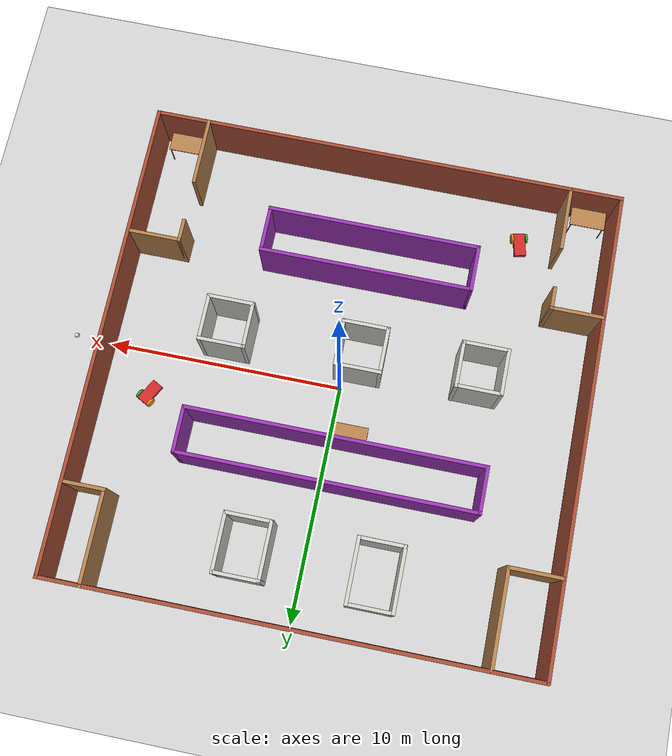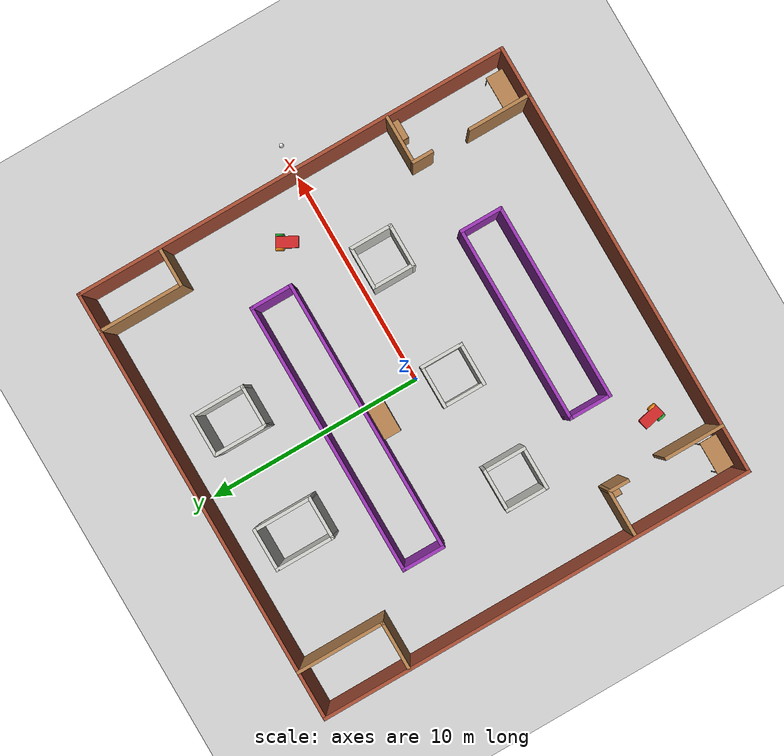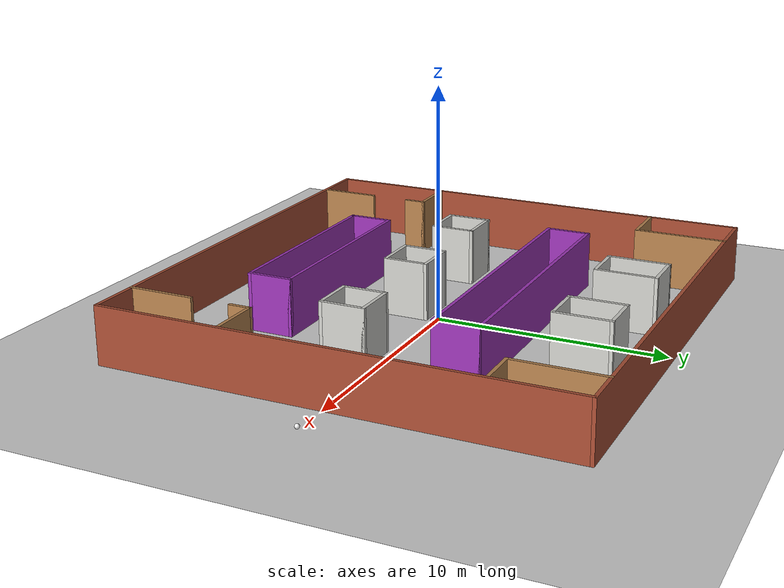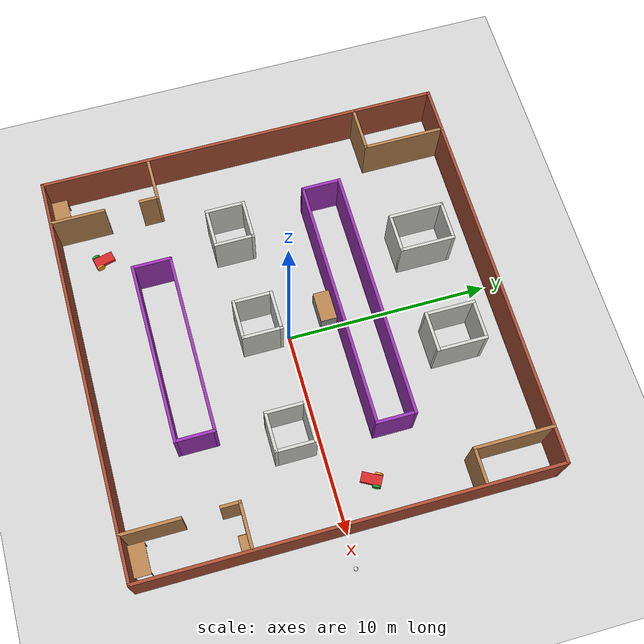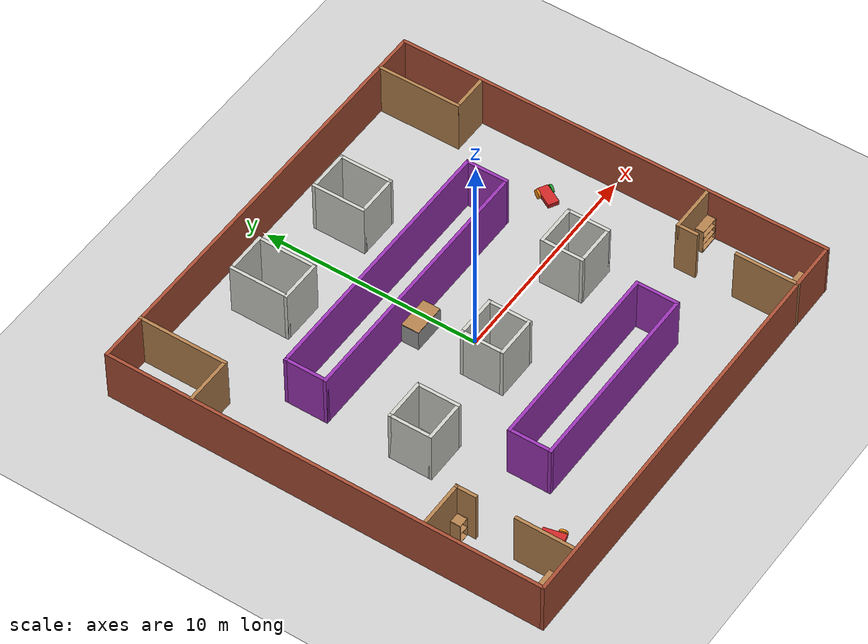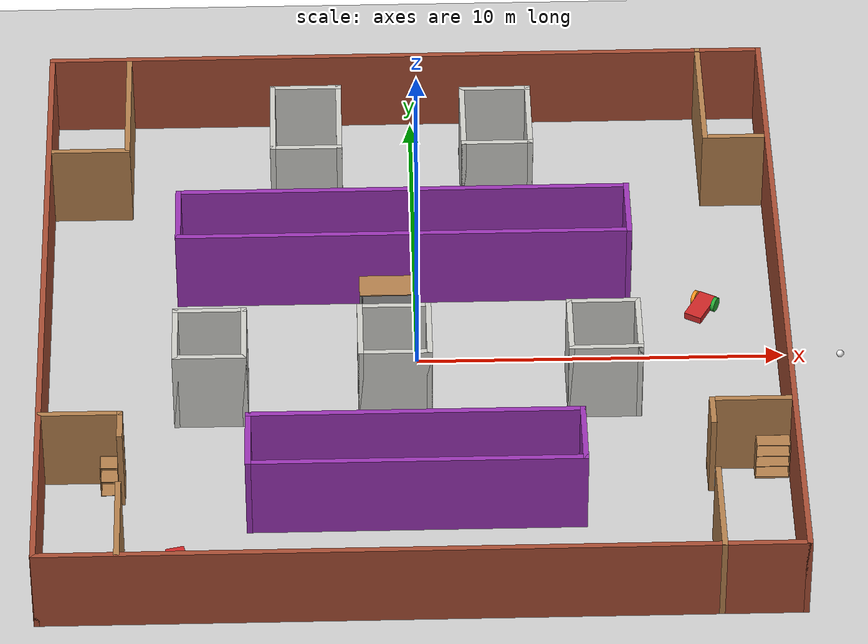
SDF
<sdf version="1.7">
 <world name="default">
  <plugin name="welcome" filename="libwelcome.so"/>
  <light name="sun" type="directional">
   <pose>0 0 10 0 -0 0</pose>
   <diffuse>0.8 0.8 0.8 1</diffuse>
   <specular>0.2 0.2 0.2 1</specular>
   <attenuation>
    <range>1000</range>
    <constant>0.9</constant>
    <linear>0.01</linear>
    <quadratic>0.001</quadratic>
   </attenuation>
   <direction>-0.5 0.1 -0.9</direction>
   <spot><inner_angle>0</inner_angle><outer_angle>0</outer_angle><falloff>0</falloff></spot>
  </light>
  <model name="ground_plane">
   <static>1</static>
   <link name="link">
    <collision name="collision">
     <geometry><plane><normal>0 0 1</normal><size>100 100</size></plane></geometry>
     <surface>
      <contact><collide_bitmask>65535</collide_bitmask></contact>
      <friction><ode><mu>100</mu><mu2>50</mu2></ode></friction>
     </surface>
    </collision>
    <visual name="visual">
     <cast_shadows>0</cast_shadows>
     <geometry><plane><normal>0 0 1</normal><size>100 100</size></plane></geometry>
     <material>
      <script><uri>file://media/materials/scripts/gazebo.material</uri><name>Gazebo/Grey</name></script>
     </material>
    </visual>
   </link>
  </model>
  <gravity>0 0 -9.8</gravity>
  <magnetic_field>6e-06 2.3e-05 -4.2e-05</magnetic_field>
  <atmosphere type="adiabatic"/>
  <physics name="default_physics" default="0" type="ode">
   <max_step_size>0.001</max_step_size>
   <real_time_factor>1</real_time_factor>
   <real_time_update_rate>1000</real_time_update_rate>
  </physics>
  <scene><ambient>0.4 0.4 0.4 1</ambient><background>0.7 0.7 0.7 1</background><shadows>1</shadows></scene>
  <spherical_coordinates>
   <surface_model>EARTH_WGS84</surface_model>
   <latitude_deg>0</latitude_deg>
   <longitude_deg>0</longitude_deg>
   <elevation>0</elevation>
   <heading_deg>0</heading_deg>
  </spherical_coordinates>
  <model name="house">
   <pose>-0.103922 0.15768 0 0 -0 0</pose>
   <link name="Wall_0">
    <collision name="Wall_0_Collision">
     <geometry><box><size>2 0.15 2.5</size></box></geometry>
     <pose>0 0 1.25 0 -0 0</pose>
    </collision>
    <visual name="Wall_0_Visual">
     <pose>0 0 1.25 0 -0 0</pose>
     <geometry><box><size>2 0.15 2.5</size></box></geometry>
     <material>
      <script><uri>file://media/materials/scripts/gazebo.material</uri><name>Gazebo/CeilingTiled</name></script>
      <ambient>1 1 1 1</ambient>
     </material>
     <meta><layer>0</layer></meta>
    </visual>
    <pose>-0.536584 -2.46607 0 0 -0 0</pose>
   </link>
   <link name="Wall_1">
    <collision name="Wall_1_Collision">
     <geometry><box><size>2 0.15 2.5</size></box></geometry>
     <pose>0 0 1.25 0 -0 0</pose>
    </collision>
    <visual name="Wall_1_Visual">
     <pose>0 0 1.25 0 -0 0</pose>
     <geometry><box><size>2 0.15 2.5</size></box></geometry>
     <material>
      <script><uri>file://media/materials/scripts/gazebo.material</uri><name>Gazebo/CeilingTiled</name></script>
      <ambient>1 1 1 1</ambient>
     </material>
     <meta><layer>0</layer></meta>
    </visual>
    <pose>0.388416 -1.54107 0 0 -0 1.5708</pose>
   </link>
   <link name="Wall_10">
    <collision name="Wall_10_Collision">
     <geometry><box><size>2 0.15 2.5</size></box></geometry>
     <pose>0 0 1.25 0 -0 0</pose>
    </collision>
    <visual name="Wall_10_Visual">
     <pose>0 0 1.25 0 -0 0</pose>
     <geometry><box><size>2 0.15 2.5</size></box></geometry>
     <material>
      <script><uri>file://media/materials/scripts/gazebo.material</uri><name>Gazebo/CeilingTiled</name></script>
      <ambient>1 1 1 1</ambient>
     </material>
     <meta><layer>0</layer></meta>
    </visual>
    <pose>-4.57919 -1.61774 0 0 -0 1.5708</pose>
   </link>
   <link name="Wall_11">
    <collision name="Wall_11_Collision">
     <geometry><box><size>2 0.15 2.5</size></box></geometry>
     <pose>0 0 1.25 0 -0 0</pose>
    </collision>
    <visual name="Wall_11_Visual">
     <pose>0 0 1.25 0 -0 0</pose>
     <geometry><box><size>2 0.15 2.5</size></box></geometry>
     <material>
      <script><uri>file://media/materials/scripts/gazebo.material</uri><name>Gazebo/CeilingTiled</name></script>
      <ambient>1 1 1 1</ambient>
     </material>
     <meta><layer>0</layer></meta>
    </visual>
    <pose>-5.50419 -0.692743 0 0 -0 3.14159</pose>
   </link>
   <link name="Wall_12">
    <collision name="Wall_12_Collision">
     <geometry><box><size>2 0.15 2.5</size></box></geometry>
     <pose>0 0 1.25 0 -0 0</pose>
    </collision>
    <visual name="Wall_12_Visual">
     <pose>0 0 1.25 0 -0 0</pose>
     <geometry><box><size>2 0.15 2.5</size></box></geometry>
     <material>
      <script><uri>file://media/materials/scripts/gazebo.material</uri><name>Gazebo/CeilingTiled</name></script>
      <ambient>1 1 1 1</ambient>
     </material>
     <meta><layer>0</layer></meta>
    </visual>
    <pose>-6.42919 -1.61774 0 0 -0 -1.5708</pose>
   </link>
   <link name="Wall_13">
    <collision name="Wall_13_Collision">
     <geometry><box><size>2 0.15 2.5</size></box></geometry>
     <pose>0 0 1.25 0 -0 0</pose>
    </collision>
    <visual name="Wall_13_Visual">
     <pose>0 0 1.25 0 -0 0</pose>
     <geometry><box><size>2 0.15 2.5</size></box></geometry>
     <material>
      <script><uri>file://media/materials/scripts/gazebo.material</uri><name>Gazebo/CeilingTiled</name></script>
      <ambient>1 1 1 1</ambient>
     </material>
     <meta><layer>0</layer></meta>
    </visual>
    <pose>-5.50419 -2.54274 0 0 -0 0</pose>
   </link>
   <link name="Wall_15">
    <collision name="Wall_15_Collision">
     <geometry><box><size>12.5 0.15 2.5</size></box></geometry>
     <pose>0 0 1.25 0 -0 0</pose>
    </collision>
    <visual name="Wall_15_Visual">
     <pose>0 0 1.25 0 -0 0</pose>
     <geometry><box><size>12.5 0.15 2.5</size></box></geometry>
     <material>
      <lighting>1</lighting>
      <script><uri>file://media/materials/scripts/gazebo.material</uri><name>Gazebo/Purple</name></script>
      <shader type="pixel"><normal_map>__default__</normal_map></shader>
      <ambient>1 0 1 1</ambient>
      <diffuse>1 0 1 1</diffuse>
      <specular>0.1 0.1 0.1 1</specular>
      <emissive>0 0 0 1</emissive>
     </material>
     <meta><layer>0</layer></meta>
    </visual>
    <pose>-0.210973 2.33564 0 0 -0 0</pose>
   </link>
   <link name="Wall_16">
    <collision name="Wall_16_Collision">
     <geometry><box><size>2 0.15 2.5</size></box></geometry>
     <pose>0 0 1.25 0 -0 0</pose>
    </collision>
    <visual name="Wall_16_Visual">
     <pose>0 0 1.25 0 -0 0</pose>
     <geometry><box><size>2 0.15 2.5</size></box></geometry>
     <material>
      <lighting>1</lighting>
      <script><uri>file://media/materials/scripts/gazebo.material</uri><name>Gazebo/Purple</name></script>
      <shader type="pixel"><normal_map>__default__</normal_map></shader>
      <ambient>1 0 1 1</ambient>
      <diffuse>1 0 1 1</diffuse>
      <specular>0.1 0.1 0.1 1</specular>
      <emissive>0 0 0 1</emissive>
     </material>
     <meta><layer>0</layer></meta>
    </visual>
    <pose>5.96403 3.26064 0 0 -0 1.5708</pose>
   </link>
   <link name="Wall_17">
    <collision name="Wall_17_Collision">
     <geometry><box><size>12.5 0.15 2.5</size></box></geometry>
     <pose>0 0 1.25 0 -0 0</pose>
    </collision>
    <visual name="Wall_17_Visual">
     <pose>0 0 1.25 0 -0 0</pose>
     <geometry><box><size>12.5 0.15 2.5</size></box></geometry>
     <material>
      <lighting>1</lighting>
      <script><uri>file://media/materials/scripts/gazebo.material</uri><name>Gazebo/Purple</name></script>
      <shader type="pixel"><normal_map>__default__</normal_map></shader>
      <ambient>1 0 1 1</ambient>
      <diffuse>1 0 1 1</diffuse>
      <specular>0.1 0.1 0.1 1</specular>
      <emissive>0 0 0 1</emissive>
     </material>
     <meta><layer>0</layer></meta>
    </visual>
    <pose>-0.210973 4.18565 0 0 -0 3.14159</pose>
   </link>
   <link name="Wall_18">
    <collision name="Wall_18_Collision">
     <geometry><box><size>2 0.15 2.5</size></box></geometry>
     <pose>0 0 1.25 0 -0 0</pose>
    </collision>
    <visual name="Wall_18_Visual">
     <pose>0 0 1.25 0 -0 0</pose>
     <geometry><box><size>2 0.15 2.5</size></box></geometry>
     <material>
      <lighting>1</lighting>
      <script><uri>file://media/materials/scripts/gazebo.material</uri><name>Gazebo/Purple</name></script>
      <shader type="pixel"><normal_map>__default__</normal_map></shader>
      <ambient>1 0 1 1</ambient>
      <diffuse>1 0 1 1</diffuse>
      <specular>0.1 0.1 0.1 1</specular>
      <emissive>0 0 0 1</emissive>
     </material>
     <meta><layer>0</layer></meta>
    </visual>
    <pose>-6.38597 3.26064 0 0 -0 -1.5708</pose>
   </link>
   <link name="Wall_2">
    <collision name="Wall_2_Collision">
     <geometry><box><size>2 0.15 2.5</size></box></geometry>
     <pose>0 0 1.25 0 -0 0</pose>
    </collision>
    <visual name="Wall_2_Visual">
     <pose>0 0 1.25 0 -0 0</pose>
     <geometry><box><size>2 0.15 2.5</size></box></geometry>
     <material>
      <script><uri>file://media/materials/scripts/gazebo.material</uri><name>Gazebo/CeilingTiled</name></script>
      <ambient>1 1 1 1</ambient>
     </material>
     <meta><layer>0</layer></meta>
    </visual>
    <pose>-0.536584 -0.616074 0 0 -0 3.14159</pose>
   </link>
   <link name="Wall_26">
    <collision name="Wall_26_Collision">
     <geometry><box><size>2 0.15 2.5</size></box></geometry>
     <pose>0 0 1.25 0 -0 0</pose>
    </collision>
    <visual name="Wall_26_Visual">
     <pose>0 0 1.25 0 -0 0</pose>
     <geometry><box><size>2 0.15 2.5</size></box></geometry>
     <material>
      <script><uri>file://media/materials/scripts/gazebo.material</uri><name>Gazebo/CeilingTiled</name></script>
      <ambient>1 1 1 1</ambient>
     </material>
     <meta><layer>0</layer></meta>
    </visual>
    <pose>-2.85415 6.03307 0 0 -0 0</pose>
   </link>
   <link name="Wall_27">
    <collision name="Wall_27_Collision">
     <geometry><box><size>2.75 0.15 2.5</size></box></geometry>
     <pose>0 0 1.25 0 -0 0</pose>
    </collision>
    <visual name="Wall_27_Visual">
     <pose>0 0 1.25 0 -0 0</pose>
     <geometry><box><size>2.75 0.15 2.5</size></box></geometry>
     <material>
      <script><uri>file://media/materials/scripts/gazebo.material</uri><name>Gazebo/CeilingTiled</name></script>
      <ambient>1 1 1 1</ambient>
     </material>
     <meta><layer>0</layer></meta>
    </visual>
    <pose>-1.92915 7.33307 0 0 -0 1.5708</pose>
   </link>
   <link name="Wall_3">
    <collision name="Wall_3_Collision">
     <geometry><box><size>2 0.15 2.5</size></box></geometry>
     <pose>0 0 1.25 0 -0 0</pose>
    </collision>
    <visual name="Wall_3_Visual">
     <pose>0 0 1.25 0 -0 0</pose>
     <geometry><box><size>2 0.15 2.5</size></box></geometry>
     <material>
      <script><uri>file://media/materials/scripts/gazebo.material</uri><name>Gazebo/CeilingTiled</name></script>
      <ambient>1 1 1 1</ambient>
     </material>
     <meta><layer>0</layer></meta>
    </visual>
    <pose>-1.46158 -1.54107 0 0 -0 -1.5708</pose>
   </link>
   <link name="Wall_30">
    <collision name="Wall_30_Collision">
     <geometry><box><size>2.75 0.15 2.5</size></box></geometry>
     <pose>0 0 1.25 0 -0 0</pose>
    </collision>
    <visual name="Wall_30_Visual">
     <pose>0 0 1.25 0 -0 0</pose>
     <geometry><box><size>2.75 0.15 2.5</size></box></geometry>
     <material>
      <script><uri>file://media/materials/scripts/gazebo.material</uri><name>Gazebo/CeilingTiled</name></script>
      <ambient>1 1 1 1</ambient>
     </material>
     <meta><layer>0</layer></meta>
    </visual>
    <pose>-3.77915 7.33307 0 0 -0 1.5708</pose>
   </link>
   <link name="Wall_31">
    <collision name="Wall_31_Collision">
     <geometry><box><size>2 0.15 2.5</size></box></geometry>
     <pose>0 0 1.25 0 -0 0</pose>
    </collision>
    <visual name="Wall_31_Visual">
     <pose>0 0 1.25 0 -0 0</pose>
     <geometry><box><size>2 0.15 2.5</size></box></geometry>
     <material>
      <script><uri>file://media/materials/scripts/gazebo.material</uri><name>Gazebo/CeilingTiled</name></script>
      <ambient>1 1 1 1</ambient>
     </material>
     <meta><layer>0</layer></meta>
    </visual>
    <pose>-2.85415 8.63307 0 0 -0 0</pose>
   </link>
   <link name="Wall_33">
    <collision name="Wall_33_Collision">
     <geometry><box><size>2 0.15 2.5</size></box></geometry>
     <pose>0 0 1.25 0 -0 0</pose>
    </collision>
    <visual name="Wall_33_Visual">
     <pose>0 0 1.25 0 -0 0</pose>
     <geometry><box><size>2 0.15 2.5</size></box></geometry>
     <material>
      <script><uri>file://media/materials/scripts/gazebo.material</uri><name>Gazebo/CeilingTiled</name></script>
      <ambient>1 1 1 1</ambient>
     </material>
     <meta><layer>0</layer></meta>
    </visual>
    <pose>2.46259 6.11826 0 0 -0 0</pose>
   </link>
   <link name="Wall_34">
    <collision name="Wall_34_Collision">
     <geometry><box><size>2.5 0.15 2.5</size></box></geometry>
     <pose>0 0 1.25 0 -0 0</pose>
    </collision>
    <visual name="Wall_34_Visual">
     <pose>0 0 1.25 0 -0 0</pose>
     <geometry><box><size>2.5 0.15 2.5</size></box></geometry>
     <material>
      <script><uri>file://media/materials/scripts/gazebo.material</uri><name>Gazebo/CeilingTiled</name></script>
      <ambient>1 1 1 1</ambient>
     </material>
     <meta><layer>0</layer></meta>
    </visual>
    <pose>3.38759 7.29326 0 0 -0 1.5708</pose>
   </link>
   <link name="Wall_35">
    <collision name="Wall_35_Collision">
     <geometry><box><size>2 0.15 2.5</size></box></geometry>
     <pose>0 0 1.25 0 -0 0</pose>
    </collision>
    <visual name="Wall_35_Visual">
     <pose>0 0 1.25 0 -0 0</pose>
     <geometry><box><size>2 0.15 2.5</size></box></geometry>
     <material>
      <script><uri>file://media/materials/scripts/gazebo.material</uri><name>Gazebo/CeilingTiled</name></script>
      <ambient>1 1 1 1</ambient>
     </material>
     <meta><layer>0</layer></meta>
    </visual>
    <pose>2.46259 8.46826 0 0 -0 3.14159</pose>
   </link>
   <link name="Wall_36">
    <collision name="Wall_36_Collision">
     <geometry><box><size>2.5 0.15 2.5</size></box></geometry>
     <pose>0 0 1.25 0 -0 0</pose>
    </collision>
    <visual name="Wall_36_Visual">
     <pose>0 0 1.25 0 -0 0</pose>
     <geometry><box><size>2.5 0.15 2.5</size></box></geometry>
     <material>
      <script><uri>file://media/materials/scripts/gazebo.material</uri><name>Gazebo/CeilingTiled</name></script>
      <ambient>1 1 1 1</ambient>
     </material>
     <meta><layer>0</layer></meta>
    </visual>
    <pose>1.53759 7.29326 0 0 -0 -1.5708</pose>
   </link>
   <link name="Wall_40">
    <collision name="Wall_40_Collision">
     <geometry><box><size>9 0.15 2.5</size></box></geometry>
     <pose>0 0 1.25 0 -0 0</pose>
    </collision>
    <visual name="Wall_40_Visual">
     <pose>0 0 1.25 0 -0 0</pose>
     <geometry><box><size>9 0.15 2.5</size></box></geometry>
     <material>
      <lighting>1</lighting>
      <script><uri>file://media/materials/scripts/gazebo.material</uri><name>Gazebo/Purple</name></script>
      <shader type="pixel"><normal_map>__default__</normal_map></shader>
      <ambient>1 0 1 1</ambient>
      <diffuse>1 0 1 1</diffuse>
      <specular>0.1 0.1 0.1 1</specular>
      <emissive>0 0 0 1</emissive>
     </material>
     <meta><layer>0</layer></meta>
    </visual>
    <pose>-0.049056 -4.81442 0 0 -0 0</pose>
   </link>
   <link name="Wall_41">
    <collision name="Wall_41_Collision">
     <geometry><box><size>2 0.15 2.5</size></box></geometry>
     <pose>0 0 1.25 0 -0 0</pose>
    </collision>
    <visual name="Wall_41_Visual">
     <pose>0 0 1.25 0 -0 0</pose>
     <geometry><box><size>2 0.15 2.5</size></box></geometry>
     <material>
      <lighting>1</lighting>
      <script><uri>file://media/materials/scripts/gazebo.material</uri><name>Gazebo/Purple</name></script>
      <shader type="pixel"><normal_map>__default__</normal_map></shader>
      <ambient>1 0 1 1</ambient>
      <diffuse>1 0 1 1</diffuse>
      <specular>0.1 0.1 0.1 1</specular>
      <emissive>0 0 0 1</emissive>
     </material>
     <meta><layer>0</layer></meta>
    </visual>
    <pose>4.37594 -5.73942 0 0 -0 -1.5708</pose>
   </link>
   <link name="Wall_42">
    <collision name="Wall_42_Collision">
     <geometry><box><size>9 0.15 2.5</size></box></geometry>
     <pose>0 0 1.25 0 -0 0</pose>
    </collision>
    <visual name="Wall_42_Visual">
     <pose>0 0 1.25 0 -0 0</pose>
     <geometry><box><size>9 0.15 2.5</size></box></geometry>
     <material>
      <lighting>1</lighting>
      <script><uri>file://media/materials/scripts/gazebo.material</uri><name>Gazebo/Purple</name></script>
      <shader type="pixel"><normal_map>__default__</normal_map></shader>
      <ambient>1 0 1 1</ambient>
      <diffuse>1 0 1 1</diffuse>
      <specular>0.1 0.1 0.1 1</specular>
      <emissive>0 0 0 1</emissive>
     </material>
     <meta><layer>0</layer></meta>
    </visual>
    <pose>-0.049056 -6.66442 0 0 -0 3.14159</pose>
   </link>
   <link name="Wall_43">
    <collision name="Wall_43_Collision">
     <geometry><box><size>2 0.15 2.5</size></box></geometry>
     <pose>0 0 1.25 0 -0 0</pose>
    </collision>
    <visual name="Wall_43_Visual">
     <pose>0 0 1.25 0 -0 0</pose>
     <geometry><box><size>2 0.15 2.5</size></box></geometry>
     <material>
      <lighting>1</lighting>
      <script><uri>file://media/materials/scripts/gazebo.material</uri><name>Gazebo/Purple</name></script>
      <shader type="pixel"><normal_map>__default__</normal_map></shader>
      <ambient>1 0 1 1</ambient>
      <diffuse>1 0 1 1</diffuse>
      <specular>0.1 0.1 0.1 1</specular>
      <emissive>0 0 0 1</emissive>
     </material>
     <meta><layer>0</layer></meta>
    </visual>
    <pose>-4.47406 -5.73942 0 0 -0 1.5708</pose>
   </link>
   <link name="Wall_5">
    <collision name="Wall_5_Collision">
     <geometry><box><size>2 0.15 2.5</size></box></geometry>
     <pose>0 0 1.25 0 -0 0</pose>
    </collision>
    <visual name="Wall_5_Visual">
     <pose>0 0 1.25 0 -0 0</pose>
     <geometry><box><size>2 0.15 2.5</size></box></geometry>
     <material>
      <script><uri>file://media/materials/scripts/gazebo.material</uri><name>Gazebo/CeilingTiled</name></script>
      <ambient>1 1 1 1</ambient>
     </material>
     <meta><layer>0</layer></meta>
    </visual>
    <pose>5.11049 -0.561674 0 0 -0 0</pose>
   </link>
   <link name="Wall_51">
    <collision name="Wall_51_Collision">
     <geometry><box><size>2.91936 0.15 2.5</size></box></geometry>
     <pose>0 0 1.25 0 -0 0</pose>
    </collision>
    <visual name="Wall_51_Visual">
     <pose>0 0 1.25 0 -0 0</pose>
     <geometry><box><size>2.91936 0.15 2.5</size></box></geometry>
     <material>
      <script><uri>file://media/materials/scripts/gazebo.material</uri><name>Gazebo/Wood</name></script>
      <ambient>1 1 1 1</ambient>
     </material>
     <meta><layer>0</layer></meta>
    </visual>
    <pose>7.806 -8.61541 0 0 -0 1.5708</pose>
   </link>
   <link name="Wall_53">
    <collision name="Wall_53_Collision">
     <geometry><box><size>1 0.15 2.5</size></box></geometry>
     <pose>0 0 1.25 0 -0 0</pose>
    </collision>
    <visual name="Wall_53_Visual">
     <pose>0 0 1.25 0 -0 0</pose>
     <geometry><box><size>1 0.15 2.5</size></box></geometry>
     <material>
      <script><uri>file://media/materials/scripts/gazebo.material</uri><name>Gazebo/Wood</name></script>
      <ambient>1 1 1 1</ambient>
     </material>
     <meta><layer>0</layer></meta>
    </visual>
    <pose>7.80558 -4.95555 0 0 -0 1.5708</pose>
   </link>
   <link name="Wall_54">
    <collision name="Wall_54_Collision">
     <geometry><box><size>2.25 0.15 2.5</size></box></geometry>
     <pose>0 0 1.25 0 -0 0</pose>
    </collision>
    <visual name="Wall_54_Visual">
     <pose>0 0 1.25 0 -0 0</pose>
     <geometry><box><size>2.25 0.15 2.5</size></box></geometry>
     <material>
      <script><uri>file://media/materials/scripts/gazebo.material</uri><name>Gazebo/Wood</name></script>
      <ambient>1 1 1 1</ambient>
     </material>
     <meta><layer>0</layer></meta>
    </visual>
    <pose>8.85558 -4.53055 0 0 -0 0</pose>
   </link>
   <link name="Wall_6">
    <collision name="Wall_6_Collision">
     <geometry><box><size>2 0.15 2.5</size></box></geometry>
     <pose>0 0 1.25 0 -0 0</pose>
    </collision>
    <visual name="Wall_6_Visual">
     <pose>0 0 1.25 0 -0 0</pose>
     <geometry><box><size>2 0.15 2.5</size></box></geometry>
     <material>
      <script><uri>file://media/materials/scripts/gazebo.material</uri><name>Gazebo/CeilingTiled</name></script>
      <ambient>1 1 1 1</ambient>
     </material>
     <meta><layer>0</layer></meta>
    </visual>
    <pose>6.03549 -1.48667 0 0 -0 -1.5708</pose>
   </link>
   <link name="Wall_60">
    <collision name="Wall_60_Collision">
     <geometry><box><size>2.77266 0.15 2.5</size></box></geometry>
     <pose>0 0 1.25 0 -0 0</pose>
    </collision>
    <visual name="Wall_60_Visual">
     <pose>0 0 1.25 0 -0 0</pose>
     <geometry><box><size>2.77266 0.15 2.5</size></box></geometry>
     <material>
      <script><uri>file://media/materials/scripts/gazebo.material</uri><name>Gazebo/Wood</name></script>
      <ambient>1 1 1 1</ambient>
     </material>
     <meta><layer>0</layer></meta>
    </visual>
    <pose>-7.847 -8.68841 0 0 -0 1.5708</pose>
   </link>
   <link name="Wall_62">
    <collision name="Wall_62_Collision">
     <geometry><box><size>1 0.15 2.5</size></box></geometry>
     <pose>0 0 1.25 0 -0 0</pose>
    </collision>
    <visual name="Wall_62_Visual">
     <pose>0 0 1.25 0 -0 0</pose>
     <geometry><box><size>1 0.15 2.5</size></box></geometry>
     <material>
      <script><uri>file://media/materials/scripts/gazebo.material</uri><name>Gazebo/Wood</name></script>
      <ambient>1 1 1 1</ambient>
     </material>
     <meta><layer>0</layer></meta>
    </visual>
    <pose>-7.84711 -5.10225 0 0 -0 1.5708</pose>
   </link>
   <link name="Wall_63">
    <collision name="Wall_63_Collision">
     <geometry><box><size>2.25 0.15 2.5</size></box></geometry>
     <pose>0 0 1.25 0 -0 0</pose>
    </collision>
    <visual name="Wall_63_Visual">
     <pose>0 0 1.25 0 -0 0</pose>
     <geometry><box><size>2.25 0.15 2.5</size></box></geometry>
     <material>
      <script><uri>file://media/materials/scripts/gazebo.material</uri><name>Gazebo/Wood</name></script>
      <ambient>1 1 1 1</ambient>
     </material>
     <meta><layer>0</layer></meta>
    </visual>
    <pose>-8.89711 -4.67725 0 0 -0 3.14159</pose>
   </link>
   <link name="Wall_66">
    <collision name="Wall_66_Collision">
     <geometry><box><size>4.1266 0.15 2.5</size></box></geometry>
     <pose>0 0 1.25 0 -0 0</pose>
    </collision>
    <visual name="Wall_66_Visual">
     <pose>0 0 1.25 0 -0 0</pose>
     <geometry><box><size>4.1266 0.15 2.5</size></box></geometry>
     <material>
      <script><uri>file://media/materials/scripts/gazebo.material</uri><name>Gazebo/Wood</name></script>
      <ambient>1 1 1 1</ambient>
     </material>
     <meta><layer>0</layer></meta>
    </visual>
    <pose>-7.824 8.01159 0 0 -0 -1.5708</pose>
   </link>
   <link name="Wall_67">
    <collision name="Wall_67_Collision">
     <geometry><box><size>2.25 0.15 2.5</size></box></geometry>
     <pose>0 0 1.25 0 -0 0</pose>
    </collision>
    <visual name="Wall_67_Visual">
     <pose>0 0 1.25 0 -0 0</pose>
     <geometry><box><size>2.25 0.15 2.5</size></box></geometry>
     <material>
      <script><uri>file://media/materials/scripts/gazebo.material</uri><name>Gazebo/Wood</name></script>
      <ambient>1 1 1 1</ambient>
     </material>
     <meta><layer>0</layer></meta>
    </visual>
    <pose>-8.87421 6.02329 0 0 -0 3.1414</pose>
   </link>
   <link name="Wall_69">
    <collision name="Wall_69_Collision">
     <geometry><box><size>3.94656 0.15 2.5</size></box></geometry>
     <pose>0 0 1.25 0 -0 0</pose>
    </collision>
    <visual name="Wall_69_Visual">
     <pose>0 0 1.25 0 -0 0</pose>
     <geometry><box><size>3.94656 0.15 2.5</size></box></geometry>
     <material>
      <script><uri>file://media/materials/scripts/gazebo.material</uri><name>Gazebo/Wood</name></script>
      <ambient>1 1 1 1</ambient>
     </material>
     <meta><layer>0</layer></meta>
    </visual>
    <pose>8.266 8.10159 0 0 -0 -1.5708</pose>
   </link>
   <link name="Wall_7">
    <collision name="Wall_7_Collision">
     <geometry><box><size>2 0.15 2.5</size></box></geometry>
     <pose>0 0 1.25 0 -0 0</pose>
    </collision>
    <visual name="Wall_7_Visual">
     <pose>0 0 1.25 0 -0 0</pose>
     <geometry><box><size>2 0.15 2.5</size></box></geometry>
     <material>
      <script><uri>file://media/materials/scripts/gazebo.material</uri><name>Gazebo/CeilingTiled</name></script>
      <ambient>1 1 1 1</ambient>
     </material>
     <meta><layer>0</layer></meta>
    </visual>
    <pose>5.11049 -2.41167 0 0 -0 3.14159</pose>
   </link>
   <link name="Wall_72">
    <collision name="Wall_72_Collision">
     <geometry><box><size>1.75 0.15 2.5</size></box></geometry>
     <pose>0 0 1.25 0 -0 0</pose>
    </collision>
    <visual name="Wall_72_Visual">
     <pose>0 0 1.25 0 -0 0</pose>
     <geometry><box><size>1.75 0.15 2.5</size></box></geometry>
     <material>
      <script><uri>file://media/materials/scripts/gazebo.material</uri><name>Gazebo/Wood</name></script>
      <ambient>1 1 1 1</ambient>
     </material>
     <meta><layer>0</layer></meta>
    </visual>
    <pose>9.06622 6.20331 0 0 -0 0.000273</pose>
   </link>
   <link name="Wall_75">
    <collision name="Wall_75_Collision">
     <geometry><box><size>20.15 0.15 2.5</size></box></geometry>
     <pose>0 0 1.25 0 -0 0</pose>
    </collision>
    <visual name="Wall_75_Visual">
     <pose>0 0 1.25 0 -0 0</pose>
     <geometry><box><size>20.15 0.15 2.5</size></box></geometry>
     <material>
      <script><uri>file://media/materials/scripts/gazebo.material</uri><name>Gazebo/Bricks</name></script>
      <ambient>1 1 1 1</ambient>
     </material>
     <meta><layer>0</layer></meta>
    </visual>
    <pose>0 -9.99991 0 0 -0 0</pose>
   </link>
   <link name="Wall_77">
    <collision name="Wall_77_Collision">
     <geometry><box><size>20.15 0.15 2.5</size></box></geometry>
     <pose>0 0 1.25 0 -0 0</pose>
    </collision>
    <visual name="Wall_77_Visual">
     <pose>0 0 1.25 0 -0 0</pose>
     <geometry><box><size>20.15 0.15 2.5</size></box></geometry>
     <material>
      <script><uri>file://media/materials/scripts/gazebo.material</uri><name>Gazebo/Bricks</name></script>
      <ambient>1 1 1 1</ambient>
     </material>
     <meta><layer>0</layer></meta>
    </visual>
    <pose>10 8.9e-05 0 0 -0 1.5708</pose>
   </link>
   <link name="Wall_79">
    <collision name="Wall_79_Collision">
     <geometry><box><size>20.15 0.15 2.5</size></box></geometry>
     <pose>0 0 1.25 0 -0 0</pose>
    </collision>
    <visual name="Wall_79_Visual">
     <pose>0 0 1.25 0 -0 0</pose>
     <geometry><box><size>20.15 0.15 2.5</size></box></geometry>
     <material>
      <script><uri>file://media/materials/scripts/gazebo.material</uri><name>Gazebo/Bricks</name></script>
      <ambient>1 1 1 1</ambient>
     </material>
     <meta><layer>0</layer></meta>
    </visual>
    <pose>-10 8.9e-05 0 0 -0 1.5708</pose>
   </link>
   <link name="Wall_8">
    <collision name="Wall_8_Collision">
     <geometry><box><size>2 0.15 2.5</size></box></geometry>
     <pose>0 0 1.25 0 -0 0</pose>
    </collision>
    <visual name="Wall_8_Visual">
     <pose>0 0 1.25 0 -0 0</pose>
     <geometry><box><size>2 0.15 2.5</size></box></geometry>
     <material>
      <script><uri>file://media/materials/scripts/gazebo.material</uri><name>Gazebo/CeilingTiled</name></script>
      <ambient>1 1 1 1</ambient>
     </material>
     <meta><layer>0</layer></meta>
    </visual>
    <pose>4.18549 -1.48667 0 0 -0 1.5708</pose>
   </link>
   <link name="Wall_81">
    <collision name="Wall_81_Collision">
     <geometry><box><size>20.15 0.15 2.5</size></box></geometry>
     <pose>0 0 1.25 0 -0 0</pose>
    </collision>
    <visual name="Wall_81_Visual">
     <pose>0 0 1.25 0 -0 0</pose>
     <geometry><box><size>20.15 0.15 2.5</size></box></geometry>
     <material>
      <script><uri>file://media/materials/scripts/gazebo.material</uri><name>Gazebo/Bricks</name></script>
      <ambient>1 1 1 1</ambient>
     </material>
     <meta><layer>0</layer></meta>
    </visual>
    <pose>0 10.0001 0 0 -0 0</pose>
   </link>
   <static>1</static>
  </model>
  <model name="wagon">
   <link name="chassis">
    <inertial>
     <mass>1</mass>
     <inertia>
      <ixx>0.166667</ixx>
      <ixy>0</ixy>
      <ixz>0</ixz>
      <iyy>0.166667</iyy>
      <iyz>0</iyz>
      <izz>0.166667</izz>
     </inertia>
    </inertial>
    <pose>0.09823 -0.107427 0.483928 0 -0 0</pose>
    <visual name="visual">
     <geometry><box><size>0.5 1 0.2</size></box></geometry>
     <material>
      <lighting>1</lighting>
      <script><uri>file://media/materials/scripts/gazebo.material</uri><name>Gazebo/Red</name></script>
      <shader type="pixel"><normal_map>__default__</normal_map></shader>
      <ambient>1 0 0 1</ambient>
      <diffuse>1 0 0 1</diffuse>
      <specular>0.1 0.1 0.1 1</specular>
      <emissive>0 0 0 1</emissive>
     </material>
    </visual>
    <collision name="collision">
     <geometry><box><size>0.5 1 0.2</size></box></geometry>
     <surface>
      <friction>
       <ode><mu>1</mu><mu2>1</mu2><fdir1>0 0 0</fdir1><slip1>0</slip1><slip2>0</slip2></ode>
       <torsional>
        <coefficient>1</coefficient>
        <patch_radius>0</patch_radius>
        <surface_radius>0</surface_radius>
        <use_patch_radius>1</use_patch_radius>
        <ode><slip>0</slip></ode>
       </torsional>
      </friction>
      <bounce><restitution_coefficient>0</restitution_coefficient><threshold>1e+06</threshold></bounce>
      <contact>
       <collide_without_contact>0</collide_without_contact>
       <collide_without_contact_bitmask>1</collide_without_contact_bitmask>
       <collide_bitmask>1</collide_bitmask>
       <ode>
        <soft_cfm>0</soft_cfm>
        <soft_erp>0.2</soft_erp>
        <kp>1e+13</kp>
        <kd>1</kd>
        <max_vel>0.01</max_vel>
        <min_depth>0</min_depth>
       </ode>
       <bullet>
        <split_impulse>1</split_impulse>
        <split_impulse_penetration_threshold>-0.01</split_impulse_penetration_threshold>
        <soft_cfm>0</soft_cfm>
        <soft_erp>0.2</soft_erp>
        <kp>1e+13</kp>
        <kd>1</kd>
       </bullet>
      </contact>
     </surface>
    </collision>
   </link>
   <link name="caster">
    <inertial>
     <mass>1</mass>
     <inertia><ixx>0.1</ixx><ixy>0</ixy><ixz>0</ixz><iyy>0.1</iyy><iyz>0</iyz><izz>0.1</izz></inertia>
    </inertial>
    <pose>0.07823 0.252573 0.387496 0 -0 0</pose>
    <visual name="visual">
     <geometry><sphere><radius>0.1</radius></sphere></geometry>
     <material>
      <lighting>1</lighting>
      <script><uri>file://media/materials/scripts/gazebo.material</uri><name>Gazebo/Blue</name></script>
      <shader type="pixel"><normal_map>__default__</normal_map></shader>
      <ambient>0 0 1 1</ambient>
      <diffuse>0 0 1 1</diffuse>
      <specular>0.1 0.1 0.1 1</specular>
      <emissive>0 0 0 1</emissive>
     </material>
    </visual>
    <collision name="collision">
     <geometry><sphere><radius>0.1</radius></sphere></geometry>
     <surface>
      <friction>
       <ode><mu>1</mu><mu2>1</mu2><fdir1>0 0 0</fdir1><slip1>0</slip1><slip2>0</slip2></ode>
       <torsional>
        <coefficient>1</coefficient>
        <patch_radius>0</patch_radius>
        <surface_radius>0</surface_radius>
        <use_patch_radius>1</use_patch_radius>
        <ode><slip>0</slip></ode>
       </torsional>
      </friction>
      <bounce><restitution_coefficient>0</restitution_coefficient><threshold>1e+06</threshold></bounce>
      <contact>
       <collide_without_contact>0</collide_without_contact>
       <collide_without_contact_bitmask>1</collide_without_contact_bitmask>
       <collide_bitmask>1</collide_bitmask>
       <ode>
        <soft_cfm>0</soft_cfm>
        <soft_erp>0.2</soft_erp>
        <kp>1e+13</kp>
        <kd>1</kd>
        <max_vel>0.01</max_vel>
        <min_depth>0</min_depth>
       </ode>
       <bullet>
        <split_impulse>1</split_impulse>
        <split_impulse_penetration_threshold>-0.01</split_impulse_penetration_threshold>
        <soft_cfm>0</soft_cfm>
        <soft_erp>0.2</soft_erp>
        <kp>1e+13</kp>
        <kd>1</kd>
       </bullet>
      </contact>
     </surface>
    </collision>
   </link>
   <link name="right_wheel">
    <inertial>
     <mass>1</mass>
     <inertia><ixx>0.145833</ixx><ixy>0</ixy><ixz>0</ixz><iyy>0.145833</iyy><iyz>0</iyz><izz>0.125</izz></inertia>
    </inertial>
    <pose>0.398249 -0.407428 0.483928 0 -0 0</pose>
    <visual name="visual">
     <pose>0 0 0 0 1.5707 0</pose>
     <geometry><cylinder><radius>0.2</radius><length>0.1</length></cylinder></geometry>
     <material>
      <lighting>1</lighting>
      <script><uri>file://media/materials/scripts/gazebo.material</uri><name>Gazebo/Orange</name></script>
      <shader type="pixel"><normal_map>__default__</normal_map></shader>
      <ambient>1 0.509 0.047 1</ambient>
      <diffuse>1 0.509 0.047 1</diffuse>
      <specular>0.5 0.5 0.5 1</specular>
      <emissive>0 0 0 1</emissive>
     </material>
    </visual>
    <collision name="collision">
     <pose>0 0 0 0 1.5707 0</pose>
     <geometry><cylinder><radius>0.2</radius><length>0.1</length></cylinder></geometry>
     <surface>
      <friction>
       <ode><mu>1</mu><mu2>1</mu2><fdir1>0 0 0</fdir1><slip1>0</slip1><slip2>0</slip2></ode>
       <torsional>
        <coefficient>1</coefficient>
        <patch_radius>0</patch_radius>
        <surface_radius>0</surface_radius>
        <use_patch_radius>1</use_patch_radius>
        <ode><slip>0</slip></ode>
       </torsional>
      </friction>
      <bounce><restitution_coefficient>0</restitution_coefficient><threshold>1e+06</threshold></bounce>
      <contact>
       <collide_without_contact>0</collide_without_contact>
       <collide_without_contact_bitmask>1</collide_without_contact_bitmask>
       <collide_bitmask>1</collide_bitmask>
       <ode>
        <soft_cfm>0</soft_cfm>
        <soft_erp>0.2</soft_erp>
        <kp>1e+13</kp>
        <kd>1</kd>
        <max_vel>0.01</max_vel>
        <min_depth>0</min_depth>
       </ode>
       <bullet>
        <split_impulse>1</split_impulse>
        <split_impulse_penetration_threshold>-0.01</split_impulse_penetration_threshold>
        <soft_cfm>0</soft_cfm>
        <soft_erp>0.2</soft_erp>
        <kp>1e+13</kp>
        <kd>1</kd>
       </bullet>
      </contact>
     </surface>
    </collision>
   </link>
   <link name="left_wheel">
    <inertial>
     <mass>1</mass>
     <inertia><ixx>0.145833</ixx><ixy>0</ixy><ixz>0</ixz><iyy>0.145833</iyy><iyz>0</iyz><izz>0.125</izz></inertia>
    </inertial>
    <pose>-0.20179 -0.407428 0.483928 0 -0 0</pose>
    <visual name="visual">
     <pose>0 0 0 0 1.5707 0</pose>
     <geometry><cylinder><radius>0.2</radius><length>0.1</length></cylinder></geometry>
     <material>
      <lighting>1</lighting>
      <script><uri>file://media/materials/scripts/gazebo.material</uri><name>Gazebo/Green</name></script>
      <shader type="pixel"><normal_map>__default__</normal_map></shader>
      <ambient>0 1 0 1</ambient>
      <diffuse>0 1 0 1</diffuse>
      <specular>0.1 0.1 0.1 1</specular>
      <emissive>0 0 0 1</emissive>
     </material>
    </visual>
    <collision name="collision">
     <pose>0 0 0 0 1.5707 0</pose>
     <geometry><cylinder><radius>0.2</radius><length>0.1</length></cylinder></geometry>
     <surface>
      <friction>
       <ode><mu>1</mu><mu2>1</mu2><fdir1>0 0 0</fdir1><slip1>0</slip1><slip2>0</slip2></ode>
       <torsional>
        <coefficient>1</coefficient>
        <patch_radius>0</patch_radius>
        <surface_radius>0</surface_radius>
        <use_patch_radius>1</use_patch_radius>
        <ode><slip>0</slip></ode>
       </torsional>
      </friction>
      <bounce><restitution_coefficient>0</restitution_coefficient><threshold>1e+06</threshold></bounce>
      <contact>
       <collide_without_contact>0</collide_without_contact>
       <collide_without_contact_bitmask>1</collide_without_contact_bitmask>
       <collide_bitmask>1</collide_bitmask>
       <ode>
        <soft_cfm>0</soft_cfm>
        <soft_erp>0.2</soft_erp>
        <kp>1e+13</kp>
        <kd>1</kd>
        <max_vel>0.01</max_vel>
        <min_depth>0</min_depth>
       </ode>
       <bullet>
        <split_impulse>1</split_impulse>
        <split_impulse_penetration_threshold>-0.01</split_impulse_penetration_threshold>
        <soft_cfm>0</soft_cfm>
        <soft_erp>0.2</soft_erp>
        <kp>1e+13</kp>
        <kd>1</kd>
       </bullet>
      </contact>
     </surface>
    </collision>
   </link>
   <joint name="chassis_JOINT_0" type="ball">
    <parent>chassis</parent>
    <child>caster</child>
    <physics>
     <ode><limit><cfm>0</cfm><erp>0.2</erp></limit><suspension><cfm>0</cfm><erp>0.2</erp></suspension></ode>
    </physics>
   </joint>
   <joint name="chassis_JOINT_1" type="revolute">
    <parent>chassis</parent>
    <child>right_wheel</child>
    <axis>
     <xyz>1 0 0</xyz>
     <limit>
      <lower>-1.79769e+308</lower>
      <upper>1.79769e+308</upper>
      <effort>-1</effort>
      <velocity>-1</velocity>
     </limit>
     <dynamics>
      <spring_reference>0</spring_reference>
      <spring_stiffness>0</spring_stiffness>
      <damping>0</damping>
     </dynamics>
    </axis>
    <physics>
     <ode><limit><cfm>0</cfm><erp>0.2</erp></limit><suspension><cfm>0</cfm><erp>0.2</erp></suspension></ode>
    </physics>
   </joint>
   <joint name="chassis_JOINT_2" type="revolute">
    <parent>chassis</parent>
    <child>left_wheel</child>
    <axis>
     <xyz>1 0 0</xyz>
     <limit>
      <lower>-1.79769e+308</lower>
      <upper>1.79769e+308</upper>
      <effort>-1</effort>
      <velocity>-1</velocity>
     </limit>
     <dynamics>
      <spring_reference>0</spring_reference>
      <spring_stiffness>0</spring_stiffness>
      <damping>0</damping>
     </dynamics>
    </axis>
    <physics>
     <ode><limit><cfm>0</cfm><erp>0.2</erp></limit><suspension><cfm>0</cfm><erp>0.2</erp></suspension></ode>
    </physics>
   </joint>
   <static>0</static>
   <pose>-6.56089 -7.79585 -0.286124 -0.005412 -6e-06 0.223909</pose>
  </model>
  <model name="wagon_0">
   <link name="chassis">
    <inertial>
     <mass>1</mass>
     <inertia>
      <ixx>0.166667</ixx>
      <ixy>0</ixy>
      <ixz>0</ixz>
      <iyy>0.166667</iyy>
      <iyz>0</iyz>
      <izz>0.166667</izz>
     </inertia>
    </inertial>
    <pose>0.09823 -0.107427 0.483928 0 -0 0</pose>
    <visual name="visual">
     <geometry><box><size>0.5 1 0.2</size></box></geometry>
     <material>
      <lighting>1</lighting>
      <script><uri>file://media/materials/scripts/gazebo.material</uri><name>Gazebo/Red</name></script>
      <shader type="pixel"><normal_map>__default__</normal_map></shader>
      <ambient>1 0 0 1</ambient>
      <diffuse>1 0 0 1</diffuse>
      <specular>0.1 0.1 0.1 1</specular>
      <emissive>0 0 0 1</emissive>
     </material>
    </visual>
    <collision name="collision">
     <geometry><box><size>0.5 1 0.2</size></box></geometry>
     <surface>
      <friction>
       <ode><mu>1</mu><mu2>1</mu2><fdir1>0 0 0</fdir1><slip1>0</slip1><slip2>0</slip2></ode>
       <torsional>
        <coefficient>1</coefficient>
        <patch_radius>0</patch_radius>
        <surface_radius>0</surface_radius>
        <use_patch_radius>1</use_patch_radius>
        <ode><slip>0</slip></ode>
       </torsional>
      </friction>
      <bounce><restitution_coefficient>0</restitution_coefficient><threshold>1e+06</threshold></bounce>
      <contact>
       <collide_without_contact>0</collide_without_contact>
       <collide_without_contact_bitmask>1</collide_without_contact_bitmask>
       <collide_bitmask>1</collide_bitmask>
       <ode>
        <soft_cfm>0</soft_cfm>
        <soft_erp>0.2</soft_erp>
        <kp>1e+13</kp>
        <kd>1</kd>
        <max_vel>0.01</max_vel>
        <min_depth>0</min_depth>
       </ode>
       <bullet>
        <split_impulse>1</split_impulse>
        <split_impulse_penetration_threshold>-0.01</split_impulse_penetration_threshold>
        <soft_cfm>0</soft_cfm>
        <soft_erp>0.2</soft_erp>
        <kp>1e+13</kp>
        <kd>1</kd>
       </bullet>
      </contact>
     </surface>
    </collision>
   </link>
   <link name="caster">
    <inertial>
     <mass>1</mass>
     <inertia><ixx>0.1</ixx><ixy>0</ixy><ixz>0</ixz><iyy>0.1</iyy><iyz>0</iyz><izz>0.1</izz></inertia>
    </inertial>
    <pose>0.07823 0.252573 0.387496 0 -0 0</pose>
    <visual name="visual">
     <geometry><sphere><radius>0.1</radius></sphere></geometry>
     <material>
      <lighting>1</lighting>
      <script><uri>file://media/materials/scripts/gazebo.material</uri><name>Gazebo/Blue</name></script>
      <shader type="pixel"><normal_map>__default__</normal_map></shader>
      <ambient>0 0 1 1</ambient>
      <diffuse>0 0 1 1</diffuse>
      <specular>0.1 0.1 0.1 1</specular>
      <emissive>0 0 0 1</emissive>
     </material>
    </visual>
    <collision name="collision">
     <geometry><sphere><radius>0.1</radius></sphere></geometry>
     <surface>
      <friction>
       <ode><mu>1</mu><mu2>1</mu2><fdir1>0 0 0</fdir1><slip1>0</slip1><slip2>0</slip2></ode>
       <torsional>
        <coefficient>1</coefficient>
        <patch_radius>0</patch_radius>
        <surface_radius>0</surface_radius>
        <use_patch_radius>1</use_patch_radius>
        <ode><slip>0</slip></ode>
       </torsional>
      </friction>
      <bounce><restitution_coefficient>0</restitution_coefficient><threshold>1e+06</threshold></bounce>
      <contact>
       <collide_without_contact>0</collide_without_contact>
       <collide_without_contact_bitmask>1</collide_without_contact_bitmask>
       <collide_bitmask>1</collide_bitmask>
       <ode>
        <soft_cfm>0</soft_cfm>
        <soft_erp>0.2</soft_erp>
        <kp>1e+13</kp>
        <kd>1</kd>
        <max_vel>0.01</max_vel>
        <min_depth>0</min_depth>
       </ode>
       <bullet>
        <split_impulse>1</split_impulse>
        <split_impulse_penetration_threshold>-0.01</split_impulse_penetration_threshold>
        <soft_cfm>0</soft_cfm>
        <soft_erp>0.2</soft_erp>
        <kp>1e+13</kp>
        <kd>1</kd>
       </bullet>
      </contact>
     </surface>
    </collision>
   </link>
   <link name="right_wheel">
    <inertial>
     <mass>1</mass>
     <inertia><ixx>0.145833</ixx><ixy>0</ixy><ixz>0</ixz><iyy>0.145833</iyy><iyz>0</iyz><izz>0.125</izz></inertia>
    </inertial>
    <pose>0.398249 -0.407428 0.483928 0 -0 0</pose>
    <visual name="visual">
     <pose>0 0 0 0 1.5707 0</pose>
     <geometry><cylinder><radius>0.2</radius><length>0.1</length></cylinder></geometry>
     <material>
      <lighting>1</lighting>
      <script><uri>file://media/materials/scripts/gazebo.material</uri><name>Gazebo/Orange</name></script>
      <shader type="pixel"><normal_map>__default__</normal_map></shader>
      <ambient>1 0.509 0.047 1</ambient>
      <diffuse>1 0.509 0.047 1</diffuse>
      <specular>0.5 0.5 0.5 1</specular>
      <emissive>0 0 0 1</emissive>
     </material>
    </visual>
    <collision name="collision">
     <pose>0 0 0 0 1.5707 0</pose>
     <geometry><cylinder><radius>0.2</radius><length>0.1</length></cylinder></geometry>
     <surface>
      <friction>
       <ode><mu>1</mu><mu2>1</mu2><fdir1>0 0 0</fdir1><slip1>0</slip1><slip2>0</slip2></ode>
       <torsional>
        <coefficient>1</coefficient>
        <patch_radius>0</patch_radius>
        <surface_radius>0</surface_radius>
        <use_patch_radius>1</use_patch_radius>
        <ode><slip>0</slip></ode>
       </torsional>
      </friction>
      <bounce><restitution_coefficient>0</restitution_coefficient><threshold>1e+06</threshold></bounce>
      <contact>
       <collide_without_contact>0</collide_without_contact>
       <collide_without_contact_bitmask>1</collide_without_contact_bitmask>
       <collide_bitmask>1</collide_bitmask>
       <ode>
        <soft_cfm>0</soft_cfm>
        <soft_erp>0.2</soft_erp>
        <kp>1e+13</kp>
        <kd>1</kd>
        <max_vel>0.01</max_vel>
        <min_depth>0</min_depth>
       </ode>
       <bullet>
        <split_impulse>1</split_impulse>
        <split_impulse_penetration_threshold>-0.01</split_impulse_penetration_threshold>
        <soft_cfm>0</soft_cfm>
        <soft_erp>0.2</soft_erp>
        <kp>1e+13</kp>
        <kd>1</kd>
       </bullet>
      </contact>
     </surface>
    </collision>
   </link>
   <link name="left_wheel">
    <inertial>
     <mass>1</mass>
     <inertia><ixx>0.145833</ixx><ixy>0</ixy><ixz>0</ixz><iyy>0.145833</iyy><iyz>0</iyz><izz>0.125</izz></inertia>
    </inertial>
    <pose>-0.20179 -0.407428 0.483928 0 -0 0</pose>
    <visual name="visual">
     <pose>0 0 0 0 1.5707 0</pose>
     <geometry><cylinder><radius>0.2</radius><length>0.1</length></cylinder></geometry>
     <material>
      <lighting>1</lighting>
      <script><uri>file://media/materials/scripts/gazebo.material</uri><name>Gazebo/Green</name></script>
      <shader type="pixel"><normal_map>__default__</normal_map></shader>
      <ambient>0 1 0 1</ambient>
      <diffuse>0 1 0 1</diffuse>
      <specular>0.1 0.1 0.1 1</specular>
      <emissive>0 0 0 1</emissive>
     </material>
    </visual>
    <collision name="collision">
     <pose>0 0 0 0 1.5707 0</pose>
     <geometry><cylinder><radius>0.2</radius><length>0.1</length></cylinder></geometry>
     <surface>
      <friction>
       <ode><mu>1</mu><mu2>1</mu2><fdir1>0 0 0</fdir1><slip1>0</slip1><slip2>0</slip2></ode>
       <torsional>
        <coefficient>1</coefficient>
        <patch_radius>0</patch_radius>
        <surface_radius>0</surface_radius>
        <use_patch_radius>1</use_patch_radius>
        <ode><slip>0</slip></ode>
       </torsional>
      </friction>
      <bounce><restitution_coefficient>0</restitution_coefficient><threshold>1e+06</threshold></bounce>
      <contact>
       <collide_without_contact>0</collide_without_contact>
       <collide_without_contact_bitmask>1</collide_without_contact_bitmask>
       <collide_bitmask>1</collide_bitmask>
       <ode>
        <soft_cfm>0</soft_cfm>
        <soft_erp>0.2</soft_erp>
        <kp>1e+13</kp>
        <kd>1</kd>
        <max_vel>0.01</max_vel>
        <min_depth>0</min_depth>
       </ode>
       <bullet>
        <split_impulse>1</split_impulse>
        <split_impulse_penetration_threshold>-0.01</split_impulse_penetration_threshold>
        <soft_cfm>0</soft_cfm>
        <soft_erp>0.2</soft_erp>
        <kp>1e+13</kp>
        <kd>1</kd>
       </bullet>
      </contact>
     </surface>
    </collision>
   </link>
   <joint name="chassis_JOINT_0" type="ball">
    <parent>chassis</parent>
    <child>caster</child>
    <physics>
     <ode><limit><cfm>0</cfm><erp>0.2</erp></limit><suspension><cfm>0</cfm><erp>0.2</erp></suspension></ode>
    </physics>
   </joint>
   <joint name="chassis_JOINT_1" type="revolute">
    <parent>chassis</parent>
    <child>right_wheel</child>
    <axis>
     <xyz>1 0 0</xyz>
     <limit>
      <lower>-1.79769e+308</lower>
      <upper>1.79769e+308</upper>
      <effort>-1</effort>
      <velocity>-1</velocity>
     </limit>
     <dynamics>
      <spring_reference>0</spring_reference>
      <spring_stiffness>0</spring_stiffness>
      <damping>0</damping>
     </dynamics>
    </axis>
    <physics>
     <ode><limit><cfm>0</cfm><erp>0.2</erp></limit><suspension><cfm>0</cfm><erp>0.2</erp></suspension></ode>
    </physics>
   </joint>
   <joint name="chassis_JOINT_2" type="revolute">
    <parent>chassis</parent>
    <child>left_wheel</child>
    <axis>
     <xyz>1 0 0</xyz>
     <limit>
      <lower>-1.79769e+308</lower>
      <upper>1.79769e+308</upper>
      <effort>-1</effort>
      <velocity>-1</velocity>
     </limit>
     <dynamics>
      <spring_reference>0</spring_reference>
      <spring_stiffness>0</spring_stiffness>
      <damping>0</damping>
     </dynamics>
    </axis>
    <physics>
     <ode><limit><cfm>0</cfm><erp>0.2</erp></limit><suspension><cfm>0</cfm><erp>0.2</erp></suspension></ode>
    </physics>
   </joint>
   <static>0</static>
   <pose>7.86392 1.6517 -0.286125 -0.005407 -8e-06 2.63802</pose>
  </model>
  <model name="table">
   <static>1</static>
   <link name="link">
    <collision name="surface">
     <pose>0 0 1 0 -0 0</pose>
     <geometry><box><size>1.5 0.8 0.03</size></box></geometry>
     <surface><friction><ode><mu>0.6</mu><mu2>0.6</mu2></ode></friction></surface>
    </collision>
    <visual name="visual1">
     <pose>0 0 1 0 -0 0</pose>
     <geometry><box><size>1.5 0.8 0.03</size></box></geometry>
     <material>
      <script><uri>file://media/materials/scripts/gazebo.material</uri><name>Gazebo/Wood</name></script>
     </material>
    </visual>
    <collision name="front_left_leg">
     <pose>0.68 0.38 0.5 0 -0 0</pose>
     <geometry><cylinder><radius>0.02</radius><length>1</length></cylinder></geometry>
    </collision>
    <visual name="front_left_leg">
     <pose>0.68 0.38 0.5 0 -0 0</pose>
     <geometry><cylinder><radius>0.02</radius><length>1</length></cylinder></geometry>
     <material>
      <script><uri>file://media/materials/scripts/gazebo.material</uri><name>Gazebo/Grey</name></script>
     </material>
    </visual>
    <collision name="front_right_leg">
     <pose>0.68 -0.38 0.5 0 -0 0</pose>
     <geometry><cylinder><radius>0.02</radius><length>1</length></cylinder></geometry>
    </collision>
    <visual name="front_right_leg">
     <pose>0.68 -0.38 0.5 0 -0 0</pose>
     <geometry><cylinder><radius>0.02</radius><length>1</length></cylinder></geometry>
     <material>
      <script><uri>file://media/materials/scripts/gazebo.material</uri><name>Gazebo/Grey</name></script>
     </material>
    </visual>
    <collision name="back_right_leg">
     <pose>-0.68 -0.38 0.5 0 -0 0</pose>
     <geometry><cylinder><radius>0.02</radius><length>1</length></cylinder></geometry>
    </collision>
    <visual name="back_right_leg">
     <pose>-0.68 -0.38 0.5 0 -0 0</pose>
     <geometry><cylinder><radius>0.02</radius><length>1</length></cylinder></geometry>
     <material>
      <script><uri>file://media/materials/scripts/gazebo.material</uri><name>Gazebo/Grey</name></script>
     </material>
    </visual>
    <collision name="back_left_leg">
     <pose>-0.68 0.38 0.5 0 -0 0</pose>
     <geometry><cylinder><radius>0.02</radius><length>1</length></cylinder></geometry>
    </collision>
    <visual name="back_left_leg">
     <pose>-0.68 0.38 0.5 0 -0 0</pose>
     <geometry><cylinder><radius>0.02</radius><length>1</length></cylinder></geometry>
     <material>
      <script><uri>file://media/materials/scripts/gazebo.material</uri><name>Gazebo/Grey</name></script>
     </material>
    </visual>
   </link>
   <pose>-0.802212 2.01362 0 0 -0 0</pose>
  </model>
  <model name="bookshelf">
   <static>1</static>
   <link name="link">
    <inertial><mass>1</mass></inertial>
    <collision name="back">
     <pose>0 0.005 0.6 0 -0 0</pose>
     <geometry><box><size>0.9 0.01 1.2</size></box></geometry>
    </collision>
    <visual name="visual1">
     <pose>0 0.005 0.6 0 -0 0</pose>
     <geometry><box><size>0.9 0.01 1.2</size></box></geometry>
     <material>
      <script><uri>file://media/materials/scripts/gazebo.material</uri><name>Gazebo/Wood</name></script>
     </material>
    </visual>
    <collision name="left_side">
     <pose>0.45 -0.195 0.6 0 -0 0</pose>
     <geometry><box><size>0.02 0.4 1.2</size></box></geometry>
    </collision>
    <visual name="visual2">
     <pose>0.45 -0.195 0.6 0 -0 0</pose>
     <geometry><box><size>0.02 0.4 1.2</size></box></geometry>
     <material>
      <script><uri>file://media/materials/scripts/gazebo.material</uri><name>Gazebo/Wood</name></script>
     </material>
    </visual>
    <collision name="right_side">
     <pose>-0.45 -0.195 0.6 0 -0 0</pose>
     <geometry><box><size>0.02 0.4 1.2</size></box></geometry>
    </collision>
    <visual name="visual3">
     <pose>-0.45 -0.195 0.6 0 -0 0</pose>
     <geometry><box><size>0.02 0.4 1.2</size></box></geometry>
     <material>
      <script><uri>file://media/materials/scripts/gazebo.material</uri><name>Gazebo/Wood</name></script>
     </material>
    </visual>
    <collision name="bottom">
     <pose>0 -0.195 0.03 0 -0 0</pose>
     <geometry><box><size>0.88 0.4 0.06</size></box></geometry>
    </collision>
    <visual name="visual4">
     <pose>0 -0.195 0.03 0 -0 0</pose>
     <geometry><box><size>0.88 0.4 0.06</size></box></geometry>
     <material>
      <script><uri>file://media/materials/scripts/gazebo.material</uri><name>Gazebo/Wood</name></script>
     </material>
    </visual>
    <collision name="top">
     <pose>0 -0.195 1.19 0 -0 0</pose>
     <geometry><box><size>0.88 0.4 0.02</size></box></geometry>
    </collision>
    <visual name="visual5">
     <pose>0 -0.195 1.19 0 -0 0</pose>
     <geometry><box><size>0.88 0.4 0.02</size></box></geometry>
     <material>
      <script><uri>file://media/materials/scripts/gazebo.material</uri><name>Gazebo/Wood</name></script>
     </material>
    </visual>
    <collision name="low_shelf">
     <pose>0 -0.195 0.43 0 -0 0</pose>
     <geometry><box><size>0.88 0.4 0.02</size></box></geometry>
    </collision>
    <visual name="visual6">
     <pose>0 -0.195 0.43 0 -0 0</pose>
     <geometry><box><size>0.88 0.4 0.02</size></box></geometry>
     <material>
      <script><uri>file://media/materials/scripts/gazebo.material</uri><name>Gazebo/Wood</name></script>
     </material>
    </visual>
    <collision name="high_shelf">
     <pose>0 -0.195 0.8 0 -0 0</pose>
     <geometry><box><size>0.88 0.4 0.02</size></box></geometry>
    </collision>
    <visual name="visual7">
     <pose>0 -0.195 0.8 0 -0 0</pose>
     <geometry><box><size>0.88 0.4 0.02</size></box></geometry>
     <material>
      <script><uri>file://media/materials/scripts/gazebo.material</uri><name>Gazebo/Wood</name></script>
     </material>
    </visual>
   </link>
   <pose>9.3519 -4.45248 0 0 -0 0</pose>
  </model>
  <model name="table_0">
   <static>1</static>
   <link name="link">
    <collision name="surface">
     <pose>0 0 1 0 -0 0</pose>
     <geometry><box><size>1.5 0.8 0.03</size></box></geometry>
     <surface><friction><ode><mu>0.6</mu><mu2>0.6</mu2></ode></friction></surface>
    </collision>
    <visual name="visual1">
     <pose>0 0 1 0 -0 0</pose>
     <geometry><box><size>1.5 0.8 0.03</size></box></geometry>
     <material>
      <script><uri>file://media/materials/scripts/gazebo.material</uri><name>Gazebo/Wood</name></script>
     </material>
    </visual>
    <collision name="front_left_leg">
     <pose>0.68 0.38 0.5 0 -0 0</pose>
     <geometry><cylinder><radius>0.02</radius><length>1</length></cylinder></geometry>
    </collision>
    <visual name="front_left_leg">
     <pose>0.68 0.38 0.5 0 -0 0</pose>
     <geometry><cylinder><radius>0.02</radius><length>1</length></cylinder></geometry>
     <material>
      <script><uri>file://media/materials/scripts/gazebo.material</uri><name>Gazebo/Grey</name></script>
     </material>
    </visual>
    <collision name="front_right_leg">
     <pose>0.68 -0.38 0.5 0 -0 0</pose>
     <geometry><cylinder><radius>0.02</radius><length>1</length></cylinder></geometry>
    </collision>
    <visual name="front_right_leg">
     <pose>0.68 -0.38 0.5 0 -0 0</pose>
     <geometry><cylinder><radius>0.02</radius><length>1</length></cylinder></geometry>
     <material>
      <script><uri>file://media/materials/scripts/gazebo.material</uri><name>Gazebo/Grey</name></script>
     </material>
    </visual>
    <collision name="back_right_leg">
     <pose>-0.68 -0.38 0.5 0 -0 0</pose>
     <geometry><cylinder><radius>0.02</radius><length>1</length></cylinder></geometry>
    </collision>
    <visual name="back_right_leg">
     <pose>-0.68 -0.38 0.5 0 -0 0</pose>
     <geometry><cylinder><radius>0.02</radius><length>1</length></cylinder></geometry>
     <material>
      <script><uri>file://media/materials/scripts/gazebo.material</uri><name>Gazebo/Grey</name></script>
     </material>
    </visual>
    <collision name="back_left_leg">
     <pose>-0.68 0.38 0.5 0 -0 0</pose>
     <geometry><cylinder><radius>0.02</radius><length>1</length></cylinder></geometry>
    </collision>
    <visual name="back_left_leg">
     <pose>-0.68 0.38 0.5 0 -0 0</pose>
     <geometry><cylinder><radius>0.02</radius><length>1</length></cylinder></geometry>
     <material>
      <script><uri>file://media/materials/scripts/gazebo.material</uri><name>Gazebo/Grey</name></script>
     </material>
    </visual>
   </link>
   <pose>8.71232 -9.32715 0 0 -0 0</pose>
  </model>
  <model name="table_1">
   <static>1</static>
   <link name="link">
    <collision name="surface">
     <pose>0 0 1 0 -0 0</pose>
     <geometry><box><size>1.5 0.8 0.03</size></box></geometry>
     <surface><friction><ode><mu>0.6</mu><mu2>0.6</mu2></ode></friction></surface>
    </collision>
    <visual name="visual1">
     <pose>0 0 1 0 -0 0</pose>
     <geometry><box><size>1.5 0.8 0.03</size></box></geometry>
     <material>
      <script><uri>file://media/materials/scripts/gazebo.material</uri><name>Gazebo/Wood</name></script>
     </material>
    </visual>
    <collision name="front_left_leg">
     <pose>0.68 0.38 0.5 0 -0 0</pose>
     <geometry><cylinder><radius>0.02</radius><length>1</length></cylinder></geometry>
    </collision>
    <visual name="front_left_leg">
     <pose>0.68 0.38 0.5 0 -0 0</pose>
     <geometry><cylinder><radius>0.02</radius><length>1</length></cylinder></geometry>
     <material>
      <script><uri>file://media/materials/scripts/gazebo.material</uri><name>Gazebo/Grey</name></script>
     </material>
    </visual>
    <collision name="front_right_leg">
     <pose>0.68 -0.38 0.5 0 -0 0</pose>
     <geometry><cylinder><radius>0.02</radius><length>1</length></cylinder></geometry>
    </collision>
    <visual name="front_right_leg">
     <pose>0.68 -0.38 0.5 0 -0 0</pose>
     <geometry><cylinder><radius>0.02</radius><length>1</length></cylinder></geometry>
     <material>
      <script><uri>file://media/materials/scripts/gazebo.material</uri><name>Gazebo/Grey</name></script>
     </material>
    </visual>
    <collision name="back_right_leg">
     <pose>-0.68 -0.38 0.5 0 -0 0</pose>
     <geometry><cylinder><radius>0.02</radius><length>1</length></cylinder></geometry>
    </collision>
    <visual name="back_right_leg">
     <pose>-0.68 -0.38 0.5 0 -0 0</pose>
     <geometry><cylinder><radius>0.02</radius><length>1</length></cylinder></geometry>
     <material>
      <script><uri>file://media/materials/scripts/gazebo.material</uri><name>Gazebo/Grey</name></script>
     </material>
    </visual>
    <collision name="back_left_leg">
     <pose>-0.68 0.38 0.5 0 -0 0</pose>
     <geometry><cylinder><radius>0.02</radius><length>1</length></cylinder></geometry>
    </collision>
    <visual name="back_left_leg">
     <pose>-0.68 0.38 0.5 0 -0 0</pose>
     <geometry><cylinder><radius>0.02</radius><length>1</length></cylinder></geometry>
     <material>
      <script><uri>file://media/materials/scripts/gazebo.material</uri><name>Gazebo/Grey</name></script>
     </material>
    </visual>
   </link>
   <pose>-9.08358 -9.34602 0 0 -0 0</pose>
  </model>
  <model name="cabinet">
   <static>1</static>
   <link name="cabinet_bottom_plate">
    <inertial>
     <pose>0 0 -1 0 -0 0</pose>
     <inertia><ixx>2.05</ixx><ixy>0</ixy><ixz>0</ixz><iyy>2.05</iyy><iyz>0</iyz><izz>2.05</izz></inertia>
     <mass>25</mass>
    </inertial>
    <collision name="cabinet_bottom_plate_geom">
     <pose>0 0 0.01 0 -0 0</pose>
     <geometry><box><size>0.45 0.45 0.02</size></box></geometry>
    </collision>
    <visual name="cabinet_bottom_plate_geom_visual">
     <pose>0 0 0.01 0 -0 0</pose>
     <geometry><box><size>0.45 0.45 0.02</size></box></geometry>
     <material>
      <script><uri>file://media/materials/scripts/gazebo.material</uri><name>Gazebo/Wood</name></script>
     </material>
    </visual>
    <collision name="cabinet_bottom_plate_geom_cabinet_back_plate">
     <pose>0.235 0 0.51 0 -0 0</pose>
     <geometry><box><size>0.02 0.45 1.02</size></box></geometry>
    </collision>
    <visual name="cabinet_bottom_plate_geom_cabinet_back_plate_visual">
     <pose>0.235 0 0.51 0 -0 0</pose>
     <geometry><box><size>0.02 0.45 1.02</size></box></geometry>
     <material>
      <script><uri>file://media/materials/scripts/gazebo.material</uri><name>Gazebo/Wood</name></script>
     </material>
    </visual>
    <collision name="cabinet_bottom_plate_geom_cabinet_left_plate">
     <pose>0 0.235 0.51 0 -0 0</pose>
     <geometry><box><size>0.45 0.02 1.02</size></box></geometry>
    </collision>
    <visual name="cabinet_bottom_plate_geom_cabinet_left_plate_visual">
     <pose>0 0.235 0.51 0 -0 0</pose>
     <geometry><box><size>0.45 0.02 1.02</size></box></geometry>
     <material>
      <script><uri>file://media/materials/scripts/gazebo.material</uri><name>Gazebo/Wood</name></script>
     </material>
    </visual>
    <collision name="cabinet_bottom_plate_geom_cabinet_middle_plate">
     <pose>0 0 0.51 0 -0 0</pose>
     <geometry><box><size>0.45 0.45 0.02</size></box></geometry>
    </collision>
    <visual name="cabinet_bottom_plate_geom_cabinet_middle_plate_visual">
     <pose>0 0 0.51 0 -0 0</pose>
     <geometry><box><size>0.45 0.45 0.02</size></box></geometry>
     <material>
      <script><uri>file://media/materials/scripts/gazebo.material</uri><name>Gazebo/Wood</name></script>
     </material>
    </visual>
    <collision name="cabinet_bottom_plate_geom_cabinet_right_plate">
     <pose>0 -0.235 0.51 0 -0 0</pose>
     <geometry><box><size>0.45 0.02 1.02</size></box></geometry>
    </collision>
    <visual name="cabinet_bottom_plate_geom_cabinet_right_plate_visual">
     <pose>0 -0.235 0.51 0 -0 0</pose>
     <geometry><box><size>0.45 0.02 1.02</size></box></geometry>
     <material>
      <script><uri>file://media/materials/scripts/gazebo.material</uri><name>Gazebo/Wood</name></script>
     </material>
    </visual>
    <collision name="cabinet_bottom_plate_geom_cabinet_top_plate">
     <pose>0 0 1.01 0 -0 0</pose>
     <geometry><box><size>0.45 0.45 0.02</size></box></geometry>
    </collision>
    <visual name="cabinet_bottom_plate_geom_cabinet_top_plate_visual">
     <pose>0 0 1.01 0 -0 0</pose>
     <geometry><box><size>0.45 0.45 0.02</size></box></geometry>
     <material>
      <script><uri>file://media/materials/scripts/gazebo.material</uri><name>Gazebo/Wood</name></script>
     </material>
    </visual>
   </link>
   <pose>-8.28524 -4.85313 0 0 -0 1.56501</pose>
  </model>
  <model name="my_ball">
   <link name="link_0">
    <inertial>
     <mass>1</mass>
     <inertia><ixx>0.1</ixx><ixy>0</ixy><ixz>0</ixz><iyy>0.1</iyy><iyz>0</iyz><izz>0.1</izz></inertia>
    </inertial>
    <visual name="visual">
     <geometry><sphere><radius>0.1</radius></sphere></geometry>
     <material>
      <lighting>1</lighting>
      <script><uri>file://media/materials/scripts/gazebo.material</uri><name>Gazebo/White</name></script>
      <shader type="normal_map_tangent_space"><normal_map>__default__</normal_map></shader>
      <ambient>1 1 1 1</ambient>
      <diffuse>1 1 1 1</diffuse>
      <specular>1 1 1 1</specular>
      <emissive>1 1 1 1</emissive>
     </material>
    </visual>
    <collision name="collision">
     <geometry><sphere><radius>0.1</radius></sphere></geometry>
     <surface>
      <friction>
       <ode><mu>1</mu><mu2>1</mu2><fdir1>0 0 0</fdir1><slip1>0</slip1><slip2>0</slip2></ode>
       <torsional>
        <coefficient>1</coefficient>
        <patch_radius>0</patch_radius>
        <surface_radius>0</surface_radius>
        <use_patch_radius>1</use_patch_radius>
        <ode><slip>0</slip></ode>
       </torsional>
      </friction>
      <bounce><restitution_coefficient>0</restitution_coefficient><threshold>1e+06</threshold></bounce>
      <contact>
       <collide_without_contact>0</collide_without_contact>
       <collide_without_contact_bitmask>1</collide_without_contact_bitmask>
       <collide_bitmask>1</collide_bitmask>
       <ode>
        <soft_cfm>0</soft_cfm>
        <soft_erp>0.2</soft_erp>
        <kp>1e+13</kp>
        <kd>1</kd>
        <max_vel>0.01</max_vel>
        <min_depth>0</min_depth>
       </ode>
       <bullet>
        <split_impulse>1</split_impulse>
        <split_impulse_penetration_threshold>-0.01</split_impulse_penetration_threshold>
        <soft_cfm>0</soft_cfm>
        <soft_erp>0.2</soft_erp>
        <kp>1e+13</kp>
        <kd>1</kd>
       </bullet>
      </contact>
     </surface>
    </collision>
   </link>
   <static>0</static>
   <pose>11.5478 -0.076395 0.1 0 -0 0</pose>
  </model>
  <model name="unit_box">
   <link name="link">
    <pose>-1.66635 0.366411 -3e-06 0 -0 0</pose>
    <inertial>
     <mass>1</mass>
     <inertia>
      <ixx>0.166667</ixx>
      <ixy>0</ixy>
      <ixz>0</ixz>
      <iyy>0.166667</iyy>
      <iyz>0</iyz>
      <izz>0.166667</izz>
     </inertia>
    </inertial>
    <visual name="visual">
     <geometry><box><size>1.5 0.8 1</size></box></geometry>
     <material>
      <script><name>Gazebo/Grey</name><uri>file://media/materials/scripts/gazebo.material</uri></script>
      <shader type="pixel"><normal_map>__default__</normal_map></shader>
      <ambient>0.3 0.3 0.3 1</ambient>
      <diffuse>0.7 0.7 0.7 1</diffuse>
      <specular>0.01 0.01 0.01 1</specular>
      <emissive>0 0 0 1</emissive>
     </material>
    </visual>
    <collision name="collision">
     <geometry><box><size>1.5 0.8 1</size></box></geometry>
     <surface>
      <friction>
       <ode><mu>1</mu><mu2>1</mu2><fdir1>0 0 0</fdir1><slip1>0</slip1><slip2>0</slip2></ode>
       <torsional>
        <coefficient>1</coefficient>
        <patch_radius>0</patch_radius>
        <surface_radius>0</surface_radius>
        <use_patch_radius>1</use_patch_radius>
        <ode><slip>0</slip></ode>
       </torsional>
      </friction>
      <bounce><restitution_coefficient>0</restitution_coefficient><threshold>1e+06</threshold></bounce>
      <contact>
       <collide_without_contact>0</collide_without_contact>
       <collide_without_contact_bitmask>1</collide_without_contact_bitmask>
       <collide_bitmask>1</collide_bitmask>
       <ode>
        <soft_cfm>0</soft_cfm>
        <soft_erp>0.2</soft_erp>
        <kp>1e+13</kp>
        <kd>1</kd>
        <max_vel>0.01</max_vel>
        <min_depth>0</min_depth>
       </ode>
       <bullet>
        <split_impulse>1</split_impulse>
        <split_impulse_penetration_threshold>-0.01</split_impulse_penetration_threshold>
        <soft_cfm>0</soft_cfm>
        <soft_erp>0.2</soft_erp>
        <kp>1e+13</kp>
        <kd>1</kd>
       </bullet>
      </contact>
     </surface>
    </collision>
   </link>
   <static>0</static>
   <pose>0.867037 1.64329 0.493625 -0.000137 0.001925 -0.003559</pose>
  </model>
 </world>
</sdf>
